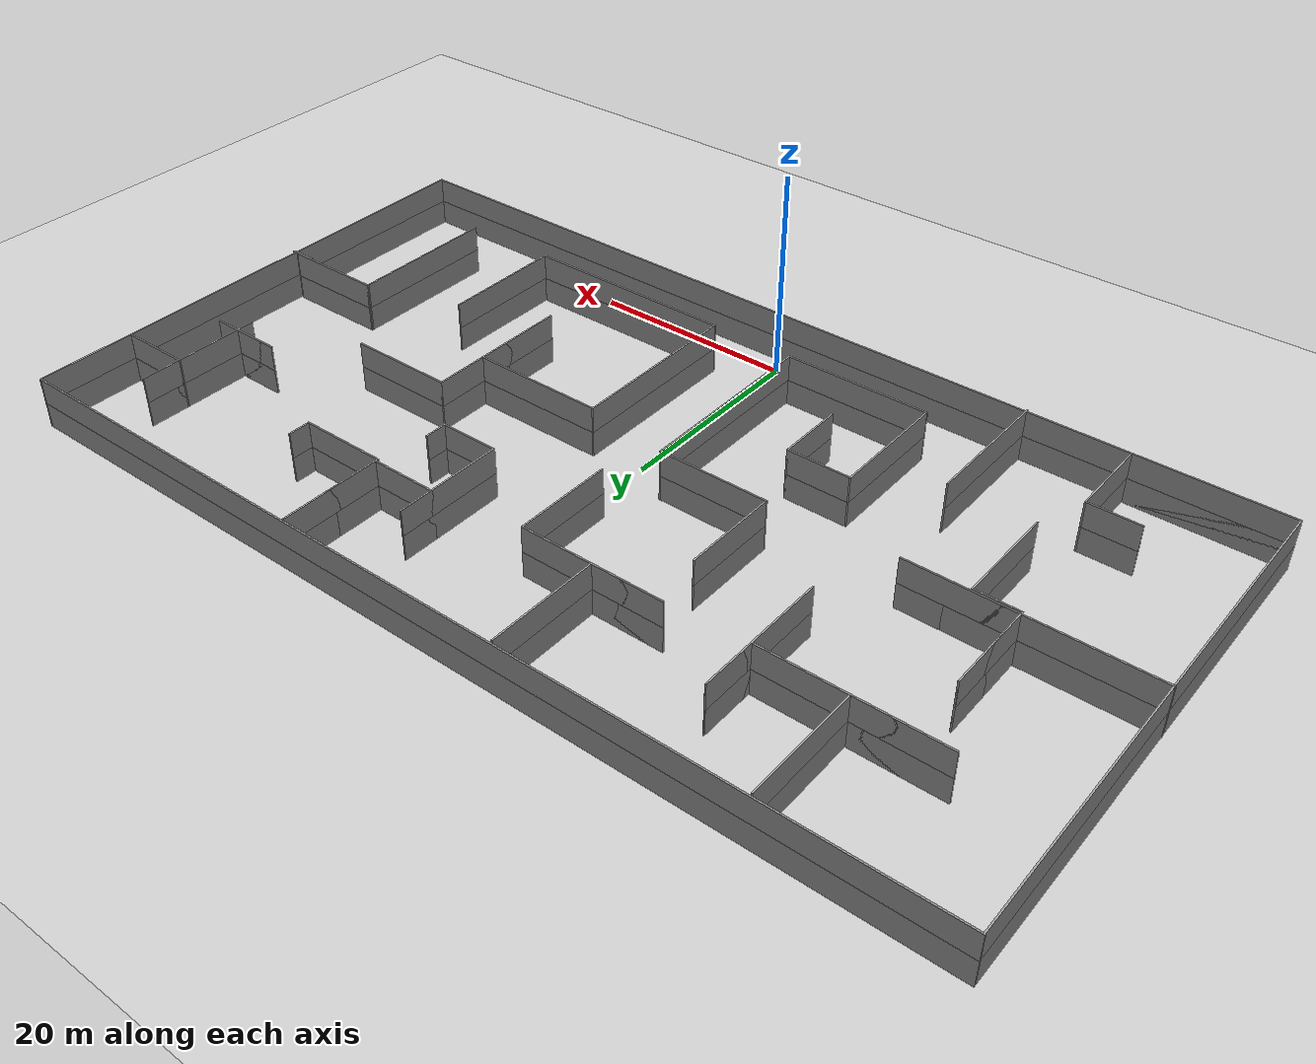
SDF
<sdf version="1.6">
 <world name="default">
  <light name="sun" type="directional">
   <pose>0 0 10 0 -0 0</pose>
   <diffuse>0.8 0.8 0.8 1</diffuse>
   <specular>0.2 0.2 0.2 1</specular>
   <attenuation>
    <range>1000</range>
    <constant>0.9</constant>
    <linear>0.01</linear>
    <quadratic>0.001</quadratic>
   </attenuation>
   <direction>-0.5 0.1 -0.9</direction>
  </light>
  <model name="ground_plane">
   <static>1</static>
   <link name="link">
    <collision name="collision">
     <geometry><plane><normal>0 0 1</normal><size>100 100</size></plane></geometry>
     <surface><friction><ode><mu>100</mu><mu2>50</mu2></ode></friction></surface>
    </collision>
    <visual name="visual">
     <cast_shadows>0</cast_shadows>
     <geometry><plane><normal>0 0 1</normal><size>100 100</size></plane></geometry>
     <material>
      <script><uri>file://media/materials/scripts/gazebo.material</uri><name>Gazebo/Grey</name></script>
     </material>
    </visual>
   </link>
  </model>
  <gravity>0 0 -9.8</gravity>
  <magnetic_field>6e-06 2.3e-05 -4.2e-05</magnetic_field>
  <atmosphere type="adiabatic"/>
  <physics name="default_physics" default="0" type="ode">
   <max_step_size>0.001</max_step_size>
   <real_time_factor>1</real_time_factor>
   <real_time_update_rate>1000</real_time_update_rate>
  </physics>
  <scene><ambient>0.4 0.4 0.4 1</ambient><background>0.7 0.7 0.7 1</background><shadows>1</shadows></scene>
  <audio><device>default</device></audio>
  <spherical_coordinates>
   <surface_model>EARTH_WGS84</surface_model>
   <latitude_deg>0</latitude_deg>
   <longitude_deg>0</longitude_deg>
   <elevation>0</elevation>
   <heading_deg>0</heading_deg>
  </spherical_coordinates>
  <model name="PaperTestRoom2">
   <pose>-1.27358 20.4941 0 0 -0 0</pose>
   <link name="Wall_10">
    <collision name="Wall_10_Collision">
     <geometry><box><size>14.25 0.15 2.5</size></box></geometry>
     <pose>0 0 1.25 0 -0 0</pose>
    </collision>
    <visual name="Wall_10_Visual">
     <pose>0 0 1.25 0 -0 0</pose>
     <geometry><box><size>14.25 0.15 2.5</size></box></geometry>
     <material>
      <script><uri>file://media/materials/scripts/gazebo.material</uri><name>Gazebo/Grey</name></script>
      <ambient>1 1 1 1</ambient>
     </material>
     <meta><layer>0</layer></meta>
    </visual>
    <pose>-39.665 -22.375 0 0 -0 0</pose>
   </link>
   <link name="Wall_11">
    <collision name="Wall_11_Collision">
     <geometry><box><size>8.5 0.15 2.5</size></box></geometry>
     <pose>0 0 1.25 0 -0 0</pose>
    </collision>
    <visual name="Wall_11_Visual">
     <pose>0 0 1.25 0 -0 0</pose>
     <geometry><box><size>8.5 0.15 2.5</size></box></geometry>
     <material>
      <script><uri>file://media/materials/scripts/gazebo.material</uri><name>Gazebo/Grey</name></script>
      <ambient>1 1 1 1</ambient>
     </material>
     <meta><layer>0</layer></meta>
    </visual>
    <pose>-32.615 -18.2 0 0 -0 1.5708</pose>
   </link>
   <link name="Wall_12">
    <collision name="Wall_12_Collision">
     <geometry><box><size>5 0.15 2.5</size></box></geometry>
     <pose>0 0 1.25 0 -0 0</pose>
    </collision>
    <visual name="Wall_12_Visual">
     <pose>0 0 1.25 0 -0 0</pose>
     <geometry><box><size>5 0.15 2.5</size></box></geometry>
     <material>
      <script><uri>file://media/materials/scripts/gazebo.material</uri><name>Gazebo/Grey</name></script>
      <ambient>1 1 1 1</ambient>
     </material>
     <meta><layer>0</layer></meta>
    </visual>
    <pose>-35.04 -14.025 0 0 -0 3.14159</pose>
   </link>
   <link name="Wall_14">
    <collision name="Wall_14_Collision">
     <geometry><box><size>13.5 0.15 2.5</size></box></geometry>
     <pose>0 0 1.25 0 -0 0</pose>
    </collision>
    <visual name="Wall_14_Visual">
     <pose>0 0 1.25 0 -0 0</pose>
     <geometry><box><size>13.5 0.15 2.5</size></box></geometry>
     <material>
      <script><uri>file://media/materials/scripts/gazebo.material</uri><name>Gazebo/Grey</name></script>
      <ambient>1 1 1 1</ambient>
     </material>
     <meta><layer>0</layer></meta>
    </visual>
    <pose>-22.9755 -15.9599 0 0 -0 1.5708</pose>
   </link>
   <link name="Wall_17">
    <collision name="Wall_17_Collision">
     <geometry><box><size>14.25 0.15 2.5</size></box></geometry>
     <pose>0 0 1.25 0 -0 0</pose>
    </collision>
    <visual name="Wall_17_Visual">
     <pose>0 0 1.25 0 -0 0</pose>
     <geometry><box><size>14.25 0.15 2.5</size></box></geometry>
     <material>
      <script><uri>file://media/materials/scripts/gazebo.material</uri><name>Gazebo/Grey</name></script>
      <ambient>1 1 1 1</ambient>
     </material>
     <meta><layer>0</layer></meta>
    </visual>
    <pose>-9.45369 -16.8689 0 0 -0 0</pose>
   </link>
   <link name="Wall_18">
    <collision name="Wall_18_Collision">
     <geometry><box><size>18.75 0.15 2.5</size></box></geometry>
     <pose>0 0 1.25 0 -0 0</pose>
    </collision>
    <visual name="Wall_18_Visual">
     <pose>0 0 1.25 0 -0 0</pose>
     <geometry><box><size>18.75 0.15 2.5</size></box></geometry>
     <material>
      <script><uri>file://media/materials/scripts/gazebo.material</uri><name>Gazebo/Grey</name></script>
      <ambient>1 1 1 1</ambient>
     </material>
     <meta><layer>0</layer></meta>
    </visual>
    <pose>-2.40369 -7.56892 0 0 -0 1.5708</pose>
   </link>
   <link name="Wall_19">
    <collision name="Wall_19_Collision">
     <geometry><box><size>10.75 0.15 2.5</size></box></geometry>
     <pose>0 0 1.25 0 -0 0</pose>
    </collision>
    <visual name="Wall_19_Visual">
     <pose>0 0 1.25 0 -0 0</pose>
     <geometry><box><size>10.75 0.15 2.5</size></box></geometry>
     <material>
      <script><uri>file://media/materials/scripts/gazebo.material</uri><name>Gazebo/Grey</name></script>
      <ambient>1 1 1 1</ambient>
     </material>
     <meta><layer>0</layer></meta>
    </visual>
    <pose>-7.70369 1.73108 0 0 -0 3.14159</pose>
   </link>
   <link name="Wall_20">
    <collision name="Wall_20_Collision">
     <geometry><box><size>9.5 0.15 2.5</size></box></geometry>
     <pose>0 0 1.25 0 -0 0</pose>
    </collision>
    <visual name="Wall_20_Visual">
     <pose>0 0 1.25 0 -0 0</pose>
     <geometry><box><size>9.5 0.15 2.5</size></box></geometry>
     <material>
      <script><uri>file://media/materials/scripts/gazebo.material</uri><name>Gazebo/Grey</name></script>
      <ambient>1 1 1 1</ambient>
     </material>
     <meta><layer>0</layer></meta>
    </visual>
    <pose>-13.0037 6.40608 0 0 -0 1.5708</pose>
   </link>
   <link name="Wall_23">
    <collision name="Wall_23_Collision">
     <geometry><box><size>12 0.15 2.5</size></box></geometry>
     <pose>0 0 1.25 0 -0 0</pose>
    </collision>
    <visual name="Wall_23_Visual">
     <pose>0 0 1.25 0 -0 0</pose>
     <geometry><box><size>12 0.15 2.5</size></box></geometry>
     <material>
      <script><uri>file://media/materials/scripts/gazebo.material</uri><name>Gazebo/Grey</name></script>
      <ambient>1 1 1 1</ambient>
     </material>
     <meta><layer>0</layer></meta>
    </visual>
    <pose>-16.5037 -10.9439 0 0 -0 1.5708</pose>
   </link>
   <link name="Wall_24">
    <collision name="Wall_24_Collision">
     <geometry><box><size>6.25 0.15 2.5</size></box></geometry>
     <pose>0 0 1.25 0 -0 0</pose>
    </collision>
    <visual name="Wall_24_Visual">
     <pose>0 0 1.25 0 -0 0</pose>
     <geometry><box><size>6.25 0.15 2.5</size></box></geometry>
     <material>
      <script><uri>file://media/materials/scripts/gazebo.material</uri><name>Gazebo/Grey</name></script>
      <ambient>1 1 1 1</ambient>
     </material>
     <meta><layer>0</layer></meta>
    </visual>
    <pose>-13.4537 -5.01892 0 0 -0 0</pose>
   </link>
   <link name="Wall_25">
    <collision name="Wall_25_Collision">
     <geometry><box><size>6.75 0.15 2.5</size></box></geometry>
     <pose>0 0 1.25 0 -0 0</pose>
    </collision>
    <visual name="Wall_25_Visual">
     <pose>0 0 1.25 0 -0 0</pose>
     <geometry><box><size>6.75 0.15 2.5</size></box></geometry>
     <material>
      <script><uri>file://media/materials/scripts/gazebo.material</uri><name>Gazebo/Grey</name></script>
      <ambient>1 1 1 1</ambient>
     </material>
     <meta><layer>0</layer></meta>
    </visual>
    <pose>-10.4037 -8.31892 0 0 -0 -1.5708</pose>
   </link>
   <link name="Wall_30">
    <collision name="Wall_30_Collision">
     <geometry><box><size>21 0.15 2.5</size></box></geometry>
     <pose>0 0 1.25 0 -0 0</pose>
    </collision>
    <visual name="Wall_30_Visual">
     <pose>0 0 1.25 0 -0 0</pose>
     <geometry><box><size>21 0.15 2.5</size></box></geometry>
     <material>
      <script><uri>file://media/materials/scripts/gazebo.material</uri><name>Gazebo/Grey</name></script>
      <ambient>1 1 1 1</ambient>
     </material>
     <meta><layer>0</layer></meta>
    </visual>
    <pose>16.3713 -16.8689 0 0 -0 0</pose>
   </link>
   <link name="Wall_31">
    <collision name="Wall_31_Collision">
     <geometry><box><size>12.25 0.15 2.5</size></box></geometry>
     <pose>0 0 1.25 0 -0 0</pose>
    </collision>
    <visual name="Wall_31_Visual">
     <pose>0 0 1.25 0 -0 0</pose>
     <geometry><box><size>12.25 0.15 2.5</size></box></geometry>
     <material>
      <script><uri>file://media/materials/scripts/gazebo.material</uri><name>Gazebo/Grey</name></script>
      <ambient>1 1 1 1</ambient>
     </material>
     <meta><layer>0</layer></meta>
    </visual>
    <pose>26.7963 -10.8189 0 0 -0 1.5708</pose>
   </link>
   <link name="Wall_34">
    <collision name="Wall_34_Collision">
     <geometry><box><size>17.5 0.15 2.5</size></box></geometry>
     <pose>0 0 1.25 0 -0 0</pose>
    </collision>
    <visual name="Wall_34_Visual">
     <pose>0 0 1.25 0 -0 0</pose>
     <geometry><box><size>17.5 0.15 2.5</size></box></geometry>
     <material>
      <script><uri>file://media/materials/scripts/gazebo.material</uri><name>Gazebo/Grey</name></script>
      <ambient>1 1 1 1</ambient>
     </material>
     <meta><layer>0</layer></meta>
    </visual>
    <pose>5.94631 -8.19392 0 0 -0 1.5708</pose>
   </link>
   <link name="Wall_35">
    <collision name="Wall_35_Collision">
     <geometry><box><size>13 0.15 2.5</size></box></geometry>
     <pose>0 0 1.25 0 -0 0</pose>
    </collision>
    <visual name="Wall_35_Visual">
     <pose>0 0 1.25 0 -0 0</pose>
     <geometry><box><size>13 0.15 2.5</size></box></geometry>
     <material>
      <script><uri>file://media/materials/scripts/gazebo.material</uri><name>Gazebo/Grey</name></script>
      <ambient>1 1 1 1</ambient>
     </material>
     <meta><layer>0</layer></meta>
    </visual>
    <pose>12.3713 0.481076 0 0 -0 0</pose>
   </link>
   <link name="Wall_36">
    <collision name="Wall_36_Collision">
     <geometry><box><size>9.25 0.15 2.5</size></box></geometry>
     <pose>0 0 1.25 0 -0 0</pose>
    </collision>
    <visual name="Wall_36_Visual">
     <pose>0 0 1.25 0 -0 0</pose>
     <geometry><box><size>9.25 0.15 2.5</size></box></geometry>
     <material>
      <script><uri>file://media/materials/scripts/gazebo.material</uri><name>Gazebo/Grey</name></script>
      <ambient>1 1 1 1</ambient>
     </material>
     <meta><layer>0</layer></meta>
    </visual>
    <pose>18.7963 -4.06892 0 0 -0 -1.5708</pose>
   </link>
   <link name="Wall_37">
    <collision name="Wall_37_Collision">
     <geometry><box><size>14.5 0.15 2.5</size></box></geometry>
     <pose>0 0 1.25 0 -0 0</pose>
    </collision>
    <visual name="Wall_37_Visual">
     <pose>0 0 1.25 0 -0 0</pose>
     <geometry><box><size>14.5 0.15 2.5</size></box></geometry>
     <material>
      <script><uri>file://media/materials/scripts/gazebo.material</uri><name>Gazebo/Grey</name></script>
      <ambient>1 1 1 1</ambient>
     </material>
     <meta><layer>0</layer></meta>
    </visual>
    <pose>18.7963 -1.44392 0 0 -0 1.5708</pose>
   </link>
   <link name="Wall_38">
    <collision name="Wall_38_Collision">
     <geometry><box><size>10.25 0.15 2.5</size></box></geometry>
     <pose>0 0 1.25 0 -0 0</pose>
    </collision>
    <visual name="Wall_38_Visual">
     <pose>0 0 1.25 0 -0 0</pose>
     <geometry><box><size>10.25 0.15 2.5</size></box></geometry>
     <material>
      <script><uri>file://media/materials/scripts/gazebo.material</uri><name>Gazebo/Grey</name></script>
      <ambient>1 1 1 1</ambient>
     </material>
     <meta><layer>0</layer></meta>
    </visual>
    <pose>23.8463 5.73108 0 0 -0 0</pose>
   </link>
   <link name="Wall_41">
    <collision name="Wall_41_Collision">
     <geometry><box><size>15 0.15 2.5</size></box></geometry>
     <pose>0 0 1.25 0 -0 0</pose>
    </collision>
    <visual name="Wall_41_Visual">
     <pose>0 0 1.25 0 -0 0</pose>
     <geometry><box><size>15 0.15 2.5</size></box></geometry>
     <material>
      <script><uri>file://media/materials/scripts/gazebo.material</uri><name>Gazebo/Grey</name></script>
      <ambient>1 1 1 1</ambient>
     </material>
     <meta><layer>0</layer></meta>
    </visual>
    <pose>36.1307 -9.29131 0 0 -0 1.5708</pose>
   </link>
   <link name="Wall_42">
    <collision name="Wall_42_Collision">
     <geometry><box><size>10 0.15 2.5</size></box></geometry>
     <pose>0 0 1.25 0 -0 0</pose>
    </collision>
    <visual name="Wall_42_Visual">
     <pose>0 0 1.25 0 -0 0</pose>
     <geometry><box><size>10 0.15 2.5</size></box></geometry>
     <material>
      <script><uri>file://media/materials/scripts/gazebo.material</uri><name>Gazebo/Grey</name></script>
      <ambient>1 1 1 1</ambient>
     </material>
     <meta><layer>0</layer></meta>
    </visual>
    <pose>41.0556 -1.86631 0 0 -0 0</pose>
   </link>
   <link name="Wall_44">
    <collision name="Wall_44_Collision">
     <geometry><box><size>2.75 0.15 2.5</size></box></geometry>
     <pose>0 0 1.25 0 -0 0</pose>
    </collision>
    <visual name="Wall_44_Visual">
     <pose>0 0 1.25 0 -0 0</pose>
     <geometry><box><size>2.75 0.15 2.5</size></box></geometry>
     <material>
      <script><uri>file://media/materials/scripts/gazebo.material</uri><name>Gazebo/Grey</name></script>
      <ambient>1 1 1 1</ambient>
     </material>
     <meta><layer>0</layer></meta>
    </visual>
    <pose>45.4491 -1.98643 0 0 -0 0</pose>
   </link>
   <link name="Wall_48">
    <collision name="Wall_48_Collision">
     <geometry><box><size>7 0.15 2.5</size></box></geometry>
     <pose>0 0 1.25 0 -0 0</pose>
    </collision>
    <visual name="Wall_48_Visual">
     <pose>0 0 1.25 0 -0 0</pose>
     <geometry><box><size>7 0.15 2.5</size></box></geometry>
     <material>
      <script><uri>file://media/materials/scripts/gazebo.material</uri><name>Gazebo/Grey</name></script>
      <ambient>1 1 1 1</ambient>
     </material>
     <meta><layer>0</layer></meta>
    </visual>
    <pose>42.8737 17.9027 0 0 -0 3.14159</pose>
   </link>
   <link name="Wall_49">
    <collision name="Wall_49_Collision">
     <geometry><box><size>4 0.15 2.5</size></box></geometry>
     <pose>0 0 1.25 0 -0 0</pose>
    </collision>
    <visual name="Wall_49_Visual">
     <pose>0 0 1.25 0 -0 0</pose>
     <geometry><box><size>4 0.15 2.5</size></box></geometry>
     <material>
      <script><uri>file://media/materials/scripts/gazebo.material</uri><name>Gazebo/Grey</name></script>
      <ambient>1 1 1 1</ambient>
     </material>
     <meta><layer>0</layer></meta>
    </visual>
    <pose>39.4487 19.8277 0 0 -0 1.5708</pose>
   </link>
   <link name="Wall_50">
    <collision name="Wall_50_Collision">
     <geometry><box><size>12.25 0.15 2.5</size></box></geometry>
     <pose>0 0 1.25 0 -0 0</pose>
    </collision>
    <visual name="Wall_50_Visual">
     <pose>0 0 1.25 0 -0 0</pose>
     <geometry><box><size>12.25 0.15 2.5</size></box></geometry>
     <material>
      <script><uri>file://media/materials/scripts/gazebo.material</uri><name>Gazebo/Grey</name></script>
      <ambient>1 1 1 1</ambient>
     </material>
     <meta><layer>0</layer></meta>
    </visual>
    <pose>39.4487 15.7027 0 0 -0 -1.5708</pose>
   </link>
   <link name="Wall_51">
    <collision name="Wall_51_Collision">
     <geometry><box><size>1.75 0.15 2.5</size></box></geometry>
     <pose>0 0 1.25 0 -0 0</pose>
    </collision>
    <visual name="Wall_51_Visual">
     <pose>0 0 1.25 0 -0 0</pose>
     <geometry><box><size>1.75 0.15 2.5</size></box></geometry>
     <material>
      <script><uri>file://media/materials/scripts/gazebo.material</uri><name>Gazebo/Grey</name></script>
      <ambient>1 1 1 1</ambient>
     </material>
     <meta><layer>0</layer></meta>
    </visual>
    <pose>39.4487 10.4527 0 0 -0 1.5708</pose>
   </link>
   <link name="Wall_52">
    <collision name="Wall_52_Collision">
     <geometry><box><size>4.75 0.15 2.5</size></box></geometry>
     <pose>0 0 1.25 0 -0 0</pose>
    </collision>
    <visual name="Wall_52_Visual">
     <pose>0 0 1.25 0 -0 0</pose>
     <geometry><box><size>4.75 0.15 2.5</size></box></geometry>
     <material>
      <script><uri>file://media/materials/scripts/gazebo.material</uri><name>Gazebo/Grey</name></script>
      <ambient>1 1 1 1</ambient>
     </material>
     <meta><layer>0</layer></meta>
    </visual>
    <pose>37.1487 11.2527 0 0 -0 3.14159</pose>
   </link>
   <link name="Wall_53">
    <collision name="Wall_53_Collision">
     <geometry><box><size>7.25 0.15 2.5</size></box></geometry>
     <pose>0 0 1.25 0 -0 0</pose>
    </collision>
    <visual name="Wall_53_Visual">
     <pose>0 0 1.25 0 -0 0</pose>
     <geometry><box><size>7.25 0.15 2.5</size></box></geometry>
     <material>
      <script><uri>file://media/materials/scripts/gazebo.material</uri><name>Gazebo/Grey</name></script>
      <ambient>1 1 1 1</ambient>
     </material>
     <meta><layer>0</layer></meta>
    </visual>
    <pose>38.3987 11.2527 0 0 -0 0</pose>
   </link>
   <link name="Wall_56">
    <collision name="Wall_56_Collision">
     <geometry><box><size>2.25 0.15 2.5</size></box></geometry>
     <pose>0 0 1.25 0 -0 0</pose>
    </collision>
    <visual name="Wall_56_Visual">
     <pose>0 0 1.25 0 -0 0</pose>
     <geometry><box><size>2.25 0.15 2.5</size></box></geometry>
     <material>
      <script><uri>file://media/materials/scripts/gazebo.material</uri><name>Gazebo/Grey</name></script>
      <ambient>1 1 1 1</ambient>
     </material>
     <meta><layer>0</layer></meta>
    </visual>
    <pose>23.1582 18.2121 0 0 -0 -1.5708</pose>
   </link>
   <link name="Wall_57">
    <collision name="Wall_57_Collision">
     <geometry><box><size>8.5 0.15 2.5</size></box></geometry>
     <pose>0 0 1.25 0 -0 0</pose>
    </collision>
    <visual name="Wall_57_Visual">
     <pose>0 0 1.25 0 -0 0</pose>
     <geometry><box><size>8.5 0.15 2.5</size></box></geometry>
     <material>
      <script><uri>file://media/materials/scripts/gazebo.material</uri><name>Gazebo/Grey</name></script>
      <ambient>1 1 1 1</ambient>
     </material>
     <meta><layer>0</layer></meta>
    </visual>
    <pose>18.9832 17.1621 0 0 -0 3.14159</pose>
   </link>
   <link name="Wall_58">
    <collision name="Wall_58_Collision">
     <geometry><box><size>10.25 0.15 2.5</size></box></geometry>
     <pose>0 0 1.25 0 -0 0</pose>
    </collision>
    <visual name="Wall_58_Visual">
     <pose>0 0 1.25 0 -0 0</pose>
     <geometry><box><size>10.25 0.15 2.5</size></box></geometry>
     <material>
      <script><uri>file://media/materials/scripts/gazebo.material</uri><name>Gazebo/Grey</name></script>
      <ambient>1 1 1 1</ambient>
     </material>
     <meta><layer>0</layer></meta>
    </visual>
    <pose>14.8082 22.2121 0 0 -0 1.5708</pose>
   </link>
   <link name="Wall_59">
    <collision name="Wall_59_Collision">
     <geometry><box><size>10 0.15 2.5</size></box></geometry>
     <pose>0 0 1.25 0 -0 0</pose>
    </collision>
    <visual name="Wall_59_Visual">
     <pose>0 0 1.25 0 -0 0</pose>
     <geometry><box><size>10 0.15 2.5</size></box></geometry>
     <material>
      <script><uri>file://media/materials/scripts/gazebo.material</uri><name>Gazebo/Grey</name></script>
      <ambient>1 1 1 1</ambient>
     </material>
     <meta><layer>0</layer></meta>
    </visual>
    <pose>14.8082 22.3371 0 0 -0 -1.5708</pose>
   </link>
   <link name="Wall_6">
    <collision name="Wall_6_Collision">
     <geometry><box><size>93 0.15 2.5</size></box></geometry>
     <pose>0 0 1.25 0 -0 0</pose>
    </collision>
    <visual name="Wall_6_Visual">
     <pose>0 0 1.25 0 -0 0</pose>
     <geometry><box><size>93 0.15 2.5</size></box></geometry>
     <material>
      <script><uri>file://media/materials/scripts/gazebo.material</uri><name>Gazebo/Grey</name></script>
      <ambient>1 1 1 1</ambient>
     </material>
     <meta><layer>0</layer></meta>
    </visual>
    <pose>-0.040017 -22.375 0 0 -0 0</pose>
   </link>
   <link name="Wall_60">
    <collision name="Wall_60_Collision">
     <geometry><box><size>6.5 0.15 2.5</size></box></geometry>
     <pose>0 0 1.25 0 -0 0</pose>
    </collision>
    <visual name="Wall_60_Visual">
     <pose>0 0 1.25 0 -0 0</pose>
     <geometry><box><size>6.5 0.15 2.5</size></box></geometry>
     <material>
      <script><uri>file://media/materials/scripts/gazebo.material</uri><name>Gazebo/Grey</name></script>
      <ambient>1 1 1 1</ambient>
     </material>
     <meta><layer>0</layer></meta>
    </visual>
    <pose>11.6332 17.4121 0 0 -0 3.14159</pose>
   </link>
   <link name="Wall_61">
    <collision name="Wall_61_Collision">
     <geometry><box><size>3.5 0.15 2.5</size></box></geometry>
     <pose>0 0 1.25 0 -0 0</pose>
    </collision>
    <visual name="Wall_61_Visual">
     <pose>0 0 1.25 0 -0 0</pose>
     <geometry><box><size>3.5 0.15 2.5</size></box></geometry>
     <material>
      <script><uri>file://media/materials/scripts/gazebo.material</uri><name>Gazebo/Grey</name></script>
      <ambient>1 1 1 1</ambient>
     </material>
     <meta><layer>0</layer></meta>
    </visual>
    <pose>8.45816 19.0871 0 0 -0 1.5708</pose>
   </link>
   <link name="Wall_62">
    <collision name="Wall_62_Collision">
     <geometry><box><size>10.75 0.15 2.5</size></box></geometry>
     <pose>0 0 1.25 0 -0 0</pose>
    </collision>
    <visual name="Wall_62_Visual">
     <pose>0 0 1.25 0 -0 0</pose>
     <geometry><box><size>10.75 0.15 2.5</size></box></geometry>
     <material>
      <script><uri>file://media/materials/scripts/gazebo.material</uri><name>Gazebo/Grey</name></script>
      <ambient>1 1 1 1</ambient>
     </material>
     <meta><layer>0</layer></meta>
    </visual>
    <pose>8.45816 15.4621 0 0 -0 -1.5708</pose>
   </link>
   <link name="Wall_63">
    <collision name="Wall_63_Collision">
     <geometry><box><size>5.75 0.15 2.5</size></box></geometry>
     <pose>0 0 1.25 0 -0 0</pose>
    </collision>
    <visual name="Wall_63_Visual">
     <pose>0 0 1.25 0 -0 0</pose>
     <geometry><box><size>5.75 0.15 2.5</size></box></geometry>
     <material>
      <script><uri>file://media/materials/scripts/gazebo.material</uri><name>Gazebo/Grey</name></script>
      <ambient>1 1 1 1</ambient>
     </material>
     <meta><layer>0</layer></meta>
    </visual>
    <pose>11.2582 10.1621 0 0 -0 0</pose>
   </link>
   <link name="Wall_64">
    <collision name="Wall_64_Collision">
     <geometry><box><size>2.25 0.15 2.5</size></box></geometry>
     <pose>0 0 1.25 0 -0 0</pose>
    </collision>
    <visual name="Wall_64_Visual">
     <pose>0 0 1.25 0 -0 0</pose>
     <geometry><box><size>2.25 0.15 2.5</size></box></geometry>
     <material>
      <script><uri>file://media/materials/scripts/gazebo.material</uri><name>Gazebo/Grey</name></script>
      <ambient>1 1 1 1</ambient>
     </material>
     <meta><layer>0</layer></meta>
    </visual>
    <pose>14.0582 11.2121 0 0 -0 1.5708</pose>
   </link>
   <link name="Wall_67">
    <collision name="Wall_67_Collision">
     <geometry><box><size>11 0.15 2.5</size></box></geometry>
     <pose>0 0 1.25 0 -0 0</pose>
    </collision>
    <visual name="Wall_67_Visual">
     <pose>0 0 1.25 0 -0 0</pose>
     <geometry><box><size>11 0.15 2.5</size></box></geometry>
     <material>
      <script><uri>file://media/materials/scripts/gazebo.material</uri><name>Gazebo/Grey</name></script>
      <ambient>1 1 1 1</ambient>
     </material>
     <meta><layer>0</layer></meta>
    </visual>
    <pose>-7.26444 21.7016 0 0 -0 -1.5708</pose>
   </link>
   <link name="Wall_68">
    <collision name="Wall_68_Collision">
     <geometry><box><size>7 0.15 2.5</size></box></geometry>
     <pose>0 0 1.25 0 -0 0</pose>
    </collision>
    <visual name="Wall_68_Visual">
     <pose>0 0 1.25 0 -0 0</pose>
     <geometry><box><size>7 0.15 2.5</size></box></geometry>
     <material>
      <script><uri>file://media/materials/scripts/gazebo.material</uri><name>Gazebo/Grey</name></script>
      <ambient>1 1 1 1</ambient>
     </material>
     <meta><layer>0</layer></meta>
    </visual>
    <pose>-10.6894 16.2766 0 0 -0 3.14159</pose>
   </link>
   <link name="Wall_69">
    <collision name="Wall_69_Collision">
     <geometry><box><size>14 0.15 2.5</size></box></geometry>
     <pose>0 0 1.25 0 -0 0</pose>
    </collision>
    <visual name="Wall_69_Visual">
     <pose>0 0 1.25 0 -0 0</pose>
     <geometry><box><size>14 0.15 2.5</size></box></geometry>
     <material>
      <script><uri>file://media/materials/scripts/gazebo.material</uri><name>Gazebo/Grey</name></script>
      <ambient>1 1 1 1</ambient>
     </material>
     <meta><layer>0</layer></meta>
    </visual>
    <pose>-7.18944 16.2766 0 0 -0 0</pose>
   </link>
   <link name="Wall_7">
    <collision name="Wall_7_Collision">
     <geometry><box><size>50 0.15 2.5</size></box></geometry>
     <pose>0 0 1.25 0 -0 0</pose>
    </collision>
    <visual name="Wall_7_Visual">
     <pose>0 0 1.25 0 -0 0</pose>
     <geometry><box><size>50 0.15 2.5</size></box></geometry>
     <material>
      <script><uri>file://media/materials/scripts/gazebo.material</uri><name>Gazebo/Grey</name></script>
      <ambient>1 1 1 1</ambient>
     </material>
     <meta><layer>0</layer></meta>
    </visual>
    <pose>46.385 2.55 0 0 -0 1.5708</pose>
   </link>
   <link name="Wall_70">
    <collision name="Wall_70_Collision">
     <geometry><box><size>9.75 0.15 2.5</size></box></geometry>
     <pose>0 0 1.25 0 -0 0</pose>
    </collision>
    <visual name="Wall_70_Visual">
     <pose>0 0 1.25 0 -0 0</pose>
     <geometry><box><size>9.75 0.15 2.5</size></box></geometry>
     <material>
      <script><uri>file://media/materials/scripts/gazebo.material</uri><name>Gazebo/Grey</name></script>
      <ambient>1 1 1 1</ambient>
     </material>
     <meta><layer>0</layer></meta>
    </visual>
    <pose>-0.264437 11.4766 0 0 -0 -1.5708</pose>
   </link>
   <link name="Wall_75">
    <collision name="Wall_75_Collision">
     <geometry><box><size>11.5 0.15 2.5</size></box></geometry>
     <pose>0 0 1.25 0 -0 0</pose>
    </collision>
    <visual name="Wall_75_Visual">
     <pose>0 0 1.25 0 -0 0</pose>
     <geometry><box><size>11.5 0.15 2.5</size></box></geometry>
     <material>
      <script><uri>file://media/materials/scripts/gazebo.material</uri><name>Gazebo/Grey</name></script>
      <ambient>1 1 1 1</ambient>
     </material>
     <meta><layer>0</layer></meta>
    </visual>
    <pose>-29.9196 21.4516 0 0 -0 -1.5708</pose>
   </link>
   <link name="Wall_76">
    <collision name="Wall_76_Collision">
     <geometry><box><size>8.5 0.15 2.5</size></box></geometry>
     <pose>0 0 1.25 0 -0 0</pose>
    </collision>
    <visual name="Wall_76_Visual">
     <pose>0 0 1.25 0 -0 0</pose>
     <geometry><box><size>8.5 0.15 2.5</size></box></geometry>
     <material>
      <script><uri>file://media/materials/scripts/gazebo.material</uri><name>Gazebo/Grey</name></script>
      <ambient>1 1 1 1</ambient>
     </material>
     <meta><layer>0</layer></meta>
    </visual>
    <pose>-34.0946 15.7766 0 0 -0 3.14159</pose>
   </link>
   <link name="Wall_77">
    <collision name="Wall_77_Collision">
     <geometry><box><size>16.75 0.15 2.5</size></box></geometry>
     <pose>0 0 1.25 0 -0 0</pose>
    </collision>
    <visual name="Wall_77_Visual">
     <pose>0 0 1.25 0 -0 0</pose>
     <geometry><box><size>16.75 0.15 2.5</size></box></geometry>
     <material>
      <script><uri>file://media/materials/scripts/gazebo.material</uri><name>Gazebo/Grey</name></script>
      <ambient>1 1 1 1</ambient>
     </material>
     <meta><layer>0</layer></meta>
    </visual>
    <pose>-29.9696 15.7766 0 0 -0 0</pose>
   </link>
   <link name="Wall_78">
    <collision name="Wall_78_Collision">
     <geometry><box><size>5.5 0.15 2.5</size></box></geometry>
     <pose>0 0 1.25 0 -0 0</pose>
    </collision>
    <visual name="Wall_78_Visual">
     <pose>0 0 1.25 0 -0 0</pose>
     <geometry><box><size>5.5 0.15 2.5</size></box></geometry>
     <material>
      <script><uri>file://media/materials/scripts/gazebo.material</uri><name>Gazebo/Grey</name></script>
      <ambient>1 1 1 1</ambient>
     </material>
     <meta><layer>0</layer></meta>
    </visual>
    <pose>-21.6696 18.4516 0 0 -0 1.5708</pose>
   </link>
   <link name="Wall_79">
    <collision name="Wall_79_Collision">
     <geometry><box><size>13.25 0.15 2.5</size></box></geometry>
     <pose>0 0 1.25 0 -0 0</pose>
    </collision>
    <visual name="Wall_79_Visual">
     <pose>0 0 1.25 0 -0 0</pose>
     <geometry><box><size>13.25 0.15 2.5</size></box></geometry>
     <material>
      <script><uri>file://media/materials/scripts/gazebo.material</uri><name>Gazebo/Grey</name></script>
      <ambient>1 1 1 1</ambient>
     </material>
     <meta><layer>0</layer></meta>
    </visual>
    <pose>-21.6696 14.5766 0 0 -0 -1.5708</pose>
   </link>
   <link name="Wall_8">
    <collision name="Wall_8_Collision">
     <geometry><box><size>93.25 0.15 2.5</size></box></geometry>
     <pose>0 0 1.25 0 -0 0</pose>
    </collision>
    <visual name="Wall_8_Visual">
     <pose>0 0 1.25 0 -0 0</pose>
     <geometry><box><size>93.25 0.15 2.5</size></box></geometry>
     <material>
      <script><uri>file://media/materials/scripts/gazebo.material</uri><name>Gazebo/Grey</name></script>
      <ambient>1 1 1 1</ambient>
     </material>
     <meta><layer>0</layer></meta>
    </visual>
    <pose>-0.165017 27.475 0 0 -0 3.14159</pose>
   </link>
   <link name="Wall_84">
    <collision name="Wall_84_Collision">
     <geometry><box><size>22 0.15 2.5</size></box></geometry>
     <pose>0 0 1.25 0 -0 0</pose>
    </collision>
    <visual name="Wall_84_Visual">
     <pose>0 0 1.25 0 -0 0</pose>
     <geometry><box><size>22 0.15 2.5</size></box></geometry>
     <material>
      <script><uri>file://media/materials/scripts/gazebo.material</uri><name>Gazebo/Grey</name></script>
      <ambient>1 1 1 1</ambient>
     </material>
     <meta><layer>0</layer></meta>
    </visual>
    <pose>-35.8241 1.07321 0 0 -0 0</pose>
   </link>
   <link name="Wall_85">
    <collision name="Wall_85_Collision">
     <geometry><box><size>10.25 0.15 2.5</size></box></geometry>
     <pose>0 0 1.25 0 -0 0</pose>
    </collision>
    <visual name="Wall_85_Visual">
     <pose>0 0 1.25 0 -0 0</pose>
     <geometry><box><size>10.25 0.15 2.5</size></box></geometry>
     <material>
      <script><uri>file://media/materials/scripts/gazebo.material</uri><name>Gazebo/Grey</name></script>
      <ambient>1 1 1 1</ambient>
     </material>
     <meta><layer>0</layer></meta>
    </visual>
    <pose>-29.9491 1.07321 0 0 -0 3.14159</pose>
   </link>
   <link name="Wall_86">
    <collision name="Wall_86_Collision">
     <geometry><box><size>9 0.15 2.5</size></box></geometry>
     <pose>0 0 1.25 0 -0 0</pose>
    </collision>
    <visual name="Wall_86_Visual">
     <pose>0 0 1.25 0 -0 0</pose>
     <geometry><box><size>9 0.15 2.5</size></box></geometry>
     <material>
      <script><uri>file://media/materials/scripts/gazebo.material</uri><name>Gazebo/Grey</name></script>
      <ambient>1 1 1 1</ambient>
     </material>
     <meta><layer>0</layer></meta>
    </visual>
    <pose>-34.9991 5.49821 0 0 -0 1.5708</pose>
   </link>
   <link name="Wall_87">
    <collision name="Wall_87_Collision">
     <geometry><box><size>9.25 0.15 2.5</size></box></geometry>
     <pose>0 0 1.25 0 -0 0</pose>
    </collision>
    <visual name="Wall_87_Visual">
     <pose>0 0 1.25 0 -0 0</pose>
     <geometry><box><size>9.25 0.15 2.5</size></box></geometry>
     <material>
      <script><uri>file://media/materials/scripts/gazebo.material</uri><name>Gazebo/Grey</name></script>
      <ambient>1 1 1 1</ambient>
     </material>
     <meta><layer>0</layer></meta>
    </visual>
    <pose>-34.9991 5.37321 0 0 -0 -1.5708</pose>
   </link>
   <link name="Wall_88">
    <collision name="Wall_88_Collision">
     <geometry><box><size>4.25 0.15 2.5</size></box></geometry>
     <pose>0 0 1.25 0 -0 0</pose>
    </collision>
    <visual name="Wall_88_Visual">
     <pose>0 0 1.25 0 -0 0</pose>
     <geometry><box><size>4.25 0.15 2.5</size></box></geometry>
     <material>
      <script><uri>file://media/materials/scripts/gazebo.material</uri><name>Gazebo/Grey</name></script>
      <ambient>1 1 1 1</ambient>
     </material>
     <meta><layer>0</layer></meta>
    </visual>
    <pose>-32.9491 0.82321 0 0 -0 0</pose>
   </link>
   <link name="Wall_89">
    <collision name="Wall_89_Collision">
     <geometry><box><size>10.25 0.15 2.5</size></box></geometry>
     <pose>0 0 1.25 0 -0 0</pose>
    </collision>
    <visual name="Wall_89_Visual">
     <pose>0 0 1.25 0 -0 0</pose>
     <geometry><box><size>10.25 0.15 2.5</size></box></geometry>
     <material>
      <script><uri>file://media/materials/scripts/gazebo.material</uri><name>Gazebo/Grey</name></script>
      <ambient>1 1 1 1</ambient>
     </material>
     <meta><layer>0</layer></meta>
    </visual>
    <pose>-30.8991 -4.22679 0 0 -0 -1.5708</pose>
   </link>
   <link name="Wall_9">
    <collision name="Wall_9_Collision">
     <geometry><box><size>50 0.15 2.5</size></box></geometry>
     <pose>0 0 1.25 0 -0 0</pose>
    </collision>
    <visual name="Wall_9_Visual">
     <pose>0 0 1.25 0 -0 0</pose>
     <geometry><box><size>50 0.15 2.5</size></box></geometry>
     <material>
      <script><uri>file://media/materials/scripts/gazebo.material</uri><name>Gazebo/Grey</name></script>
      <ambient>1 1 1 1</ambient>
     </material>
     <meta><layer>0</layer></meta>
    </visual>
    <pose>-46.715 2.55 0 0 -0 -1.5708</pose>
   </link>
   <static>1</static>
  </model>
  <model name="PaperTestRoom2_clone">
   <pose>-1.27358 20.494 2.5 0 -0 0</pose>
   <link name="Wall_10">
    <collision name="Wall_10_Collision">
     <geometry><box><size>14.25 0.15 2.5</size></box></geometry>
     <pose>0 0 1.25 0 -0 0</pose>
    </collision>
    <visual name="Wall_10_Visual">
     <pose>0 0 1.25 0 -0 0</pose>
     <geometry><box><size>14.25 0.15 2.5</size></box></geometry>
     <material>
      <script><uri>file://media/materials/scripts/gazebo.material</uri><name>Gazebo/Grey</name></script>
      <ambient>1 1 1 1</ambient>
     </material>
     <meta><layer>0</layer></meta>
    </visual>
    <pose>-39.665 -22.375 0 0 -0 0</pose>
   </link>
   <link name="Wall_11">
    <collision name="Wall_11_Collision">
     <geometry><box><size>8.5 0.15 2.5</size></box></geometry>
     <pose>0 0 1.25 0 -0 0</pose>
    </collision>
    <visual name="Wall_11_Visual">
     <pose>0 0 1.25 0 -0 0</pose>
     <geometry><box><size>8.5 0.15 2.5</size></box></geometry>
     <material>
      <script><uri>file://media/materials/scripts/gazebo.material</uri><name>Gazebo/Grey</name></script>
      <ambient>1 1 1 1</ambient>
     </material>
     <meta><layer>0</layer></meta>
    </visual>
    <pose>-32.615 -18.2 0 0 -0 1.5708</pose>
   </link>
   <link name="Wall_12">
    <collision name="Wall_12_Collision">
     <geometry><box><size>5 0.15 2.5</size></box></geometry>
     <pose>0 0 1.25 0 -0 0</pose>
    </collision>
    <visual name="Wall_12_Visual">
     <pose>0 0 1.25 0 -0 0</pose>
     <geometry><box><size>5 0.15 2.5</size></box></geometry>
     <material>
      <script><uri>file://media/materials/scripts/gazebo.material</uri><name>Gazebo/Grey</name></script>
      <ambient>1 1 1 1</ambient>
     </material>
     <meta><layer>0</layer></meta>
    </visual>
    <pose>-35.04 -14.025 0 0 -0 3.14159</pose>
   </link>
   <link name="Wall_14">
    <collision name="Wall_14_Collision">
     <geometry><box><size>13.5 0.15 2.5</size></box></geometry>
     <pose>0 0 1.25 0 -0 0</pose>
    </collision>
    <visual name="Wall_14_Visual">
     <pose>0 0 1.25 0 -0 0</pose>
     <geometry><box><size>13.5 0.15 2.5</size></box></geometry>
     <material>
      <script><uri>file://media/materials/scripts/gazebo.material</uri><name>Gazebo/Grey</name></script>
      <ambient>1 1 1 1</ambient>
     </material>
     <meta><layer>0</layer></meta>
    </visual>
    <pose>-22.9755 -15.9599 0 0 -0 1.5708</pose>
   </link>
   <link name="Wall_17">
    <collision name="Wall_17_Collision">
     <geometry><box><size>14.25 0.15 2.5</size></box></geometry>
     <pose>0 0 1.25 0 -0 0</pose>
    </collision>
    <visual name="Wall_17_Visual">
     <pose>0 0 1.25 0 -0 0</pose>
     <geometry><box><size>14.25 0.15 2.5</size></box></geometry>
     <material>
      <script><uri>file://media/materials/scripts/gazebo.material</uri><name>Gazebo/Grey</name></script>
      <ambient>1 1 1 1</ambient>
     </material>
     <meta><layer>0</layer></meta>
    </visual>
    <pose>-9.45369 -16.8689 0 0 -0 0</pose>
   </link>
   <link name="Wall_18">
    <collision name="Wall_18_Collision">
     <geometry><box><size>18.75 0.15 2.5</size></box></geometry>
     <pose>0 0 1.25 0 -0 0</pose>
    </collision>
    <visual name="Wall_18_Visual">
     <pose>0 0 1.25 0 -0 0</pose>
     <geometry><box><size>18.75 0.15 2.5</size></box></geometry>
     <material>
      <script><uri>file://media/materials/scripts/gazebo.material</uri><name>Gazebo/Grey</name></script>
      <ambient>1 1 1 1</ambient>
     </material>
     <meta><layer>0</layer></meta>
    </visual>
    <pose>-2.40369 -7.56892 0 0 -0 1.5708</pose>
   </link>
   <link name="Wall_19">
    <collision name="Wall_19_Collision">
     <geometry><box><size>10.75 0.15 2.5</size></box></geometry>
     <pose>0 0 1.25 0 -0 0</pose>
    </collision>
    <visual name="Wall_19_Visual">
     <pose>0 0 1.25 0 -0 0</pose>
     <geometry><box><size>10.75 0.15 2.5</size></box></geometry>
     <material>
      <script><uri>file://media/materials/scripts/gazebo.material</uri><name>Gazebo/Grey</name></script>
      <ambient>1 1 1 1</ambient>
     </material>
     <meta><layer>0</layer></meta>
    </visual>
    <pose>-7.70369 1.73108 0 0 -0 3.14159</pose>
   </link>
   <link name="Wall_20">
    <collision name="Wall_20_Collision">
     <geometry><box><size>9.5 0.15 2.5</size></box></geometry>
     <pose>0 0 1.25 0 -0 0</pose>
    </collision>
    <visual name="Wall_20_Visual">
     <pose>0 0 1.25 0 -0 0</pose>
     <geometry><box><size>9.5 0.15 2.5</size></box></geometry>
     <material>
      <script><uri>file://media/materials/scripts/gazebo.material</uri><name>Gazebo/Grey</name></script>
      <ambient>1 1 1 1</ambient>
     </material>
     <meta><layer>0</layer></meta>
    </visual>
    <pose>-13.0037 6.40608 0 0 -0 1.5708</pose>
   </link>
   <link name="Wall_23">
    <collision name="Wall_23_Collision">
     <geometry><box><size>12 0.15 2.5</size></box></geometry>
     <pose>0 0 1.25 0 -0 0</pose>
    </collision>
    <visual name="Wall_23_Visual">
     <pose>0 0 1.25 0 -0 0</pose>
     <geometry><box><size>12 0.15 2.5</size></box></geometry>
     <material>
      <script><uri>file://media/materials/scripts/gazebo.material</uri><name>Gazebo/Grey</name></script>
      <ambient>1 1 1 1</ambient>
     </material>
     <meta><layer>0</layer></meta>
    </visual>
    <pose>-16.5037 -10.9439 0 0 -0 1.5708</pose>
   </link>
   <link name="Wall_24">
    <collision name="Wall_24_Collision">
     <geometry><box><size>6.25 0.15 2.5</size></box></geometry>
     <pose>0 0 1.25 0 -0 0</pose>
    </collision>
    <visual name="Wall_24_Visual">
     <pose>0 0 1.25 0 -0 0</pose>
     <geometry><box><size>6.25 0.15 2.5</size></box></geometry>
     <material>
      <script><uri>file://media/materials/scripts/gazebo.material</uri><name>Gazebo/Grey</name></script>
      <ambient>1 1 1 1</ambient>
     </material>
     <meta><layer>0</layer></meta>
    </visual>
    <pose>-13.4537 -5.01892 0 0 -0 0</pose>
   </link>
   <link name="Wall_25">
    <collision name="Wall_25_Collision">
     <geometry><box><size>6.75 0.15 2.5</size></box></geometry>
     <pose>0 0 1.25 0 -0 0</pose>
    </collision>
    <visual name="Wall_25_Visual">
     <pose>0 0 1.25 0 -0 0</pose>
     <geometry><box><size>6.75 0.15 2.5</size></box></geometry>
     <material>
      <script><uri>file://media/materials/scripts/gazebo.material</uri><name>Gazebo/Grey</name></script>
      <ambient>1 1 1 1</ambient>
     </material>
     <meta><layer>0</layer></meta>
    </visual>
    <pose>-10.4037 -8.31892 0 0 -0 -1.5708</pose>
   </link>
   <link name="Wall_30">
    <collision name="Wall_30_Collision">
     <geometry><box><size>21 0.15 2.5</size></box></geometry>
     <pose>0 0 1.25 0 -0 0</pose>
    </collision>
    <visual name="Wall_30_Visual">
     <pose>0 0 1.25 0 -0 0</pose>
     <geometry><box><size>21 0.15 2.5</size></box></geometry>
     <material>
      <script><uri>file://media/materials/scripts/gazebo.material</uri><name>Gazebo/Grey</name></script>
      <ambient>1 1 1 1</ambient>
     </material>
     <meta><layer>0</layer></meta>
    </visual>
    <pose>16.3713 -16.8689 0 0 -0 0</pose>
   </link>
   <link name="Wall_31">
    <collision name="Wall_31_Collision">
     <geometry><box><size>12.25 0.15 2.5</size></box></geometry>
     <pose>0 0 1.25 0 -0 0</pose>
    </collision>
    <visual name="Wall_31_Visual">
     <pose>0 0 1.25 0 -0 0</pose>
     <geometry><box><size>12.25 0.15 2.5</size></box></geometry>
     <material>
      <script><uri>file://media/materials/scripts/gazebo.material</uri><name>Gazebo/Grey</name></script>
      <ambient>1 1 1 1</ambient>
     </material>
     <meta><layer>0</layer></meta>
    </visual>
    <pose>26.7963 -10.8189 0 0 -0 1.5708</pose>
   </link>
   <link name="Wall_34">
    <collision name="Wall_34_Collision">
     <geometry><box><size>17.5 0.15 2.5</size></box></geometry>
     <pose>0 0 1.25 0 -0 0</pose>
    </collision>
    <visual name="Wall_34_Visual">
     <pose>0 0 1.25 0 -0 0</pose>
     <geometry><box><size>17.5 0.15 2.5</size></box></geometry>
     <material>
      <script><uri>file://media/materials/scripts/gazebo.material</uri><name>Gazebo/Grey</name></script>
      <ambient>1 1 1 1</ambient>
     </material>
     <meta><layer>0</layer></meta>
    </visual>
    <pose>5.94631 -8.19392 0 0 -0 1.5708</pose>
   </link>
   <link name="Wall_35">
    <collision name="Wall_35_Collision">
     <geometry><box><size>13 0.15 2.5</size></box></geometry>
     <pose>0 0 1.25 0 -0 0</pose>
    </collision>
    <visual name="Wall_35_Visual">
     <pose>0 0 1.25 0 -0 0</pose>
     <geometry><box><size>13 0.15 2.5</size></box></geometry>
     <material>
      <script><uri>file://media/materials/scripts/gazebo.material</uri><name>Gazebo/Grey</name></script>
      <ambient>1 1 1 1</ambient>
     </material>
     <meta><layer>0</layer></meta>
    </visual>
    <pose>12.3713 0.481076 0 0 -0 0</pose>
   </link>
   <link name="Wall_36">
    <collision name="Wall_36_Collision">
     <geometry><box><size>9.25 0.15 2.5</size></box></geometry>
     <pose>0 0 1.25 0 -0 0</pose>
    </collision>
    <visual name="Wall_36_Visual">
     <pose>0 0 1.25 0 -0 0</pose>
     <geometry><box><size>9.25 0.15 2.5</size></box></geometry>
     <material>
      <script><uri>file://media/materials/scripts/gazebo.material</uri><name>Gazebo/Grey</name></script>
      <ambient>1 1 1 1</ambient>
     </material>
     <meta><layer>0</layer></meta>
    </visual>
    <pose>18.7963 -4.06892 0 0 -0 -1.5708</pose>
   </link>
   <link name="Wall_37">
    <collision name="Wall_37_Collision">
     <geometry><box><size>14.5 0.15 2.5</size></box></geometry>
     <pose>0 0 1.25 0 -0 0</pose>
    </collision>
    <visual name="Wall_37_Visual">
     <pose>0 0 1.25 0 -0 0</pose>
     <geometry><box><size>14.5 0.15 2.5</size></box></geometry>
     <material>
      <script><uri>file://media/materials/scripts/gazebo.material</uri><name>Gazebo/Grey</name></script>
      <ambient>1 1 1 1</ambient>
     </material>
     <meta><layer>0</layer></meta>
    </visual>
    <pose>18.7963 -1.44392 0 0 -0 1.5708</pose>
   </link>
   <link name="Wall_38">
    <collision name="Wall_38_Collision">
     <geometry><box><size>10.25 0.15 2.5</size></box></geometry>
     <pose>0 0 1.25 0 -0 0</pose>
    </collision>
    <visual name="Wall_38_Visual">
     <pose>0 0 1.25 0 -0 0</pose>
     <geometry><box><size>10.25 0.15 2.5</size></box></geometry>
     <material>
      <script><uri>file://media/materials/scripts/gazebo.material</uri><name>Gazebo/Grey</name></script>
      <ambient>1 1 1 1</ambient>
     </material>
     <meta><layer>0</layer></meta>
    </visual>
    <pose>23.8463 5.73108 0 0 -0 0</pose>
   </link>
   <link name="Wall_41">
    <collision name="Wall_41_Collision">
     <geometry><box><size>15 0.15 2.5</size></box></geometry>
     <pose>0 0 1.25 0 -0 0</pose>
    </collision>
    <visual name="Wall_41_Visual">
     <pose>0 0 1.25 0 -0 0</pose>
     <geometry><box><size>15 0.15 2.5</size></box></geometry>
     <material>
      <script><uri>file://media/materials/scripts/gazebo.material</uri><name>Gazebo/Grey</name></script>
      <ambient>1 1 1 1</ambient>
     </material>
     <meta><layer>0</layer></meta>
    </visual>
    <pose>36.1307 -9.29131 0 0 -0 1.5708</pose>
   </link>
   <link name="Wall_42">
    <collision name="Wall_42_Collision">
     <geometry><box><size>10 0.15 2.5</size></box></geometry>
     <pose>0 0 1.25 0 -0 0</pose>
    </collision>
    <visual name="Wall_42_Visual">
     <pose>0 0 1.25 0 -0 0</pose>
     <geometry><box><size>10 0.15 2.5</size></box></geometry>
     <material>
      <script><uri>file://media/materials/scripts/gazebo.material</uri><name>Gazebo/Grey</name></script>
      <ambient>1 1 1 1</ambient>
     </material>
     <meta><layer>0</layer></meta>
    </visual>
    <pose>41.0556 -1.86631 0 0 -0 0</pose>
   </link>
   <link name="Wall_44">
    <collision name="Wall_44_Collision">
     <geometry><box><size>2.75 0.15 2.5</size></box></geometry>
     <pose>0 0 1.25 0 -0 0</pose>
    </collision>
    <visual name="Wall_44_Visual">
     <pose>0 0 1.25 0 -0 0</pose>
     <geometry><box><size>2.75 0.15 2.5</size></box></geometry>
     <material>
      <script><uri>file://media/materials/scripts/gazebo.material</uri><name>Gazebo/Grey</name></script>
      <ambient>1 1 1 1</ambient>
     </material>
     <meta><layer>0</layer></meta>
    </visual>
    <pose>45.4491 -1.98643 0 0 -0 0</pose>
   </link>
   <link name="Wall_48">
    <collision name="Wall_48_Collision">
     <geometry><box><size>7 0.15 2.5</size></box></geometry>
     <pose>0 0 1.25 0 -0 0</pose>
    </collision>
    <visual name="Wall_48_Visual">
     <pose>0 0 1.25 0 -0 0</pose>
     <geometry><box><size>7 0.15 2.5</size></box></geometry>
     <material>
      <script><uri>file://media/materials/scripts/gazebo.material</uri><name>Gazebo/Grey</name></script>
      <ambient>1 1 1 1</ambient>
     </material>
     <meta><layer>0</layer></meta>
    </visual>
    <pose>42.8737 17.9027 0 0 -0 3.14159</pose>
   </link>
   <link name="Wall_49">
    <collision name="Wall_49_Collision">
     <geometry><box><size>4 0.15 2.5</size></box></geometry>
     <pose>0 0 1.25 0 -0 0</pose>
    </collision>
    <visual name="Wall_49_Visual">
     <pose>0 0 1.25 0 -0 0</pose>
     <geometry><box><size>4 0.15 2.5</size></box></geometry>
     <material>
      <script><uri>file://media/materials/scripts/gazebo.material</uri><name>Gazebo/Grey</name></script>
      <ambient>1 1 1 1</ambient>
     </material>
     <meta><layer>0</layer></meta>
    </visual>
    <pose>39.4487 19.8277 0 0 -0 1.5708</pose>
   </link>
   <link name="Wall_50">
    <collision name="Wall_50_Collision">
     <geometry><box><size>12.25 0.15 2.5</size></box></geometry>
     <pose>0 0 1.25 0 -0 0</pose>
    </collision>
    <visual name="Wall_50_Visual">
     <pose>0 0 1.25 0 -0 0</pose>
     <geometry><box><size>12.25 0.15 2.5</size></box></geometry>
     <material>
      <script><uri>file://media/materials/scripts/gazebo.material</uri><name>Gazebo/Grey</name></script>
      <ambient>1 1 1 1</ambient>
     </material>
     <meta><layer>0</layer></meta>
    </visual>
    <pose>39.4487 15.7027 0 0 -0 -1.5708</pose>
   </link>
   <link name="Wall_51">
    <collision name="Wall_51_Collision">
     <geometry><box><size>1.75 0.15 2.5</size></box></geometry>
     <pose>0 0 1.25 0 -0 0</pose>
    </collision>
    <visual name="Wall_51_Visual">
     <pose>0 0 1.25 0 -0 0</pose>
     <geometry><box><size>1.75 0.15 2.5</size></box></geometry>
     <material>
      <script><uri>file://media/materials/scripts/gazebo.material</uri><name>Gazebo/Grey</name></script>
      <ambient>1 1 1 1</ambient>
     </material>
     <meta><layer>0</layer></meta>
    </visual>
    <pose>39.4487 10.4527 0 0 -0 1.5708</pose>
   </link>
   <link name="Wall_52">
    <collision name="Wall_52_Collision">
     <geometry><box><size>4.75 0.15 2.5</size></box></geometry>
     <pose>0 0 1.25 0 -0 0</pose>
    </collision>
    <visual name="Wall_52_Visual">
     <pose>0 0 1.25 0 -0 0</pose>
     <geometry><box><size>4.75 0.15 2.5</size></box></geometry>
     <material>
      <script><uri>file://media/materials/scripts/gazebo.material</uri><name>Gazebo/Grey</name></script>
      <ambient>1 1 1 1</ambient>
     </material>
     <meta><layer>0</layer></meta>
    </visual>
    <pose>37.1487 11.2527 0 0 -0 3.14159</pose>
   </link>
   <link name="Wall_53">
    <collision name="Wall_53_Collision">
     <geometry><box><size>7.25 0.15 2.5</size></box></geometry>
     <pose>0 0 1.25 0 -0 0</pose>
    </collision>
    <visual name="Wall_53_Visual">
     <pose>0 0 1.25 0 -0 0</pose>
     <geometry><box><size>7.25 0.15 2.5</size></box></geometry>
     <material>
      <script><uri>file://media/materials/scripts/gazebo.material</uri><name>Gazebo/Grey</name></script>
      <ambient>1 1 1 1</ambient>
     </material>
     <meta><layer>0</layer></meta>
    </visual>
    <pose>38.3987 11.2527 0 0 -0 0</pose>
   </link>
   <link name="Wall_56">
    <collision name="Wall_56_Collision">
     <geometry><box><size>2.25 0.15 2.5</size></box></geometry>
     <pose>0 0 1.25 0 -0 0</pose>
    </collision>
    <visual name="Wall_56_Visual">
     <pose>0 0 1.25 0 -0 0</pose>
     <geometry><box><size>2.25 0.15 2.5</size></box></geometry>
     <material>
      <script><uri>file://media/materials/scripts/gazebo.material</uri><name>Gazebo/Grey</name></script>
      <ambient>1 1 1 1</ambient>
     </material>
     <meta><layer>0</layer></meta>
    </visual>
    <pose>23.1582 18.2121 0 0 -0 -1.5708</pose>
   </link>
   <link name="Wall_57">
    <collision name="Wall_57_Collision">
     <geometry><box><size>8.5 0.15 2.5</size></box></geometry>
     <pose>0 0 1.25 0 -0 0</pose>
    </collision>
    <visual name="Wall_57_Visual">
     <pose>0 0 1.25 0 -0 0</pose>
     <geometry><box><size>8.5 0.15 2.5</size></box></geometry>
     <material>
      <script><uri>file://media/materials/scripts/gazebo.material</uri><name>Gazebo/Grey</name></script>
      <ambient>1 1 1 1</ambient>
     </material>
     <meta><layer>0</layer></meta>
    </visual>
    <pose>18.9832 17.1621 0 0 -0 3.14159</pose>
   </link>
   <link name="Wall_58">
    <collision name="Wall_58_Collision">
     <geometry><box><size>10.25 0.15 2.5</size></box></geometry>
     <pose>0 0 1.25 0 -0 0</pose>
    </collision>
    <visual name="Wall_58_Visual">
     <pose>0 0 1.25 0 -0 0</pose>
     <geometry><box><size>10.25 0.15 2.5</size></box></geometry>
     <material>
      <script><uri>file://media/materials/scripts/gazebo.material</uri><name>Gazebo/Grey</name></script>
      <ambient>1 1 1 1</ambient>
     </material>
     <meta><layer>0</layer></meta>
    </visual>
    <pose>14.8082 22.2121 0 0 -0 1.5708</pose>
   </link>
   <link name="Wall_59">
    <collision name="Wall_59_Collision">
     <geometry><box><size>10 0.15 2.5</size></box></geometry>
     <pose>0 0 1.25 0 -0 0</pose>
    </collision>
    <visual name="Wall_59_Visual">
     <pose>0 0 1.25 0 -0 0</pose>
     <geometry><box><size>10 0.15 2.5</size></box></geometry>
     <material>
      <script><uri>file://media/materials/scripts/gazebo.material</uri><name>Gazebo/Grey</name></script>
      <ambient>1 1 1 1</ambient>
     </material>
     <meta><layer>0</layer></meta>
    </visual>
    <pose>14.8082 22.3371 0 0 -0 -1.5708</pose>
   </link>
   <link name="Wall_6">
    <collision name="Wall_6_Collision">
     <geometry><box><size>93 0.15 2.5</size></box></geometry>
     <pose>0 0 1.25 0 -0 0</pose>
    </collision>
    <visual name="Wall_6_Visual">
     <pose>0 0 1.25 0 -0 0</pose>
     <geometry><box><size>93 0.15 2.5</size></box></geometry>
     <material>
      <script><uri>file://media/materials/scripts/gazebo.material</uri><name>Gazebo/Grey</name></script>
      <ambient>1 1 1 1</ambient>
     </material>
     <meta><layer>0</layer></meta>
    </visual>
    <pose>-0.040017 -22.375 0 0 -0 0</pose>
   </link>
   <link name="Wall_60">
    <collision name="Wall_60_Collision">
     <geometry><box><size>6.5 0.15 2.5</size></box></geometry>
     <pose>0 0 1.25 0 -0 0</pose>
    </collision>
    <visual name="Wall_60_Visual">
     <pose>0 0 1.25 0 -0 0</pose>
     <geometry><box><size>6.5 0.15 2.5</size></box></geometry>
     <material>
      <script><uri>file://media/materials/scripts/gazebo.material</uri><name>Gazebo/Grey</name></script>
      <ambient>1 1 1 1</ambient>
     </material>
     <meta><layer>0</layer></meta>
    </visual>
    <pose>11.6332 17.4121 0 0 -0 3.14159</pose>
   </link>
   <link name="Wall_61">
    <collision name="Wall_61_Collision">
     <geometry><box><size>3.5 0.15 2.5</size></box></geometry>
     <pose>0 0 1.25 0 -0 0</pose>
    </collision>
    <visual name="Wall_61_Visual">
     <pose>0 0 1.25 0 -0 0</pose>
     <geometry><box><size>3.5 0.15 2.5</size></box></geometry>
     <material>
      <script><uri>file://media/materials/scripts/gazebo.material</uri><name>Gazebo/Grey</name></script>
      <ambient>1 1 1 1</ambient>
     </material>
     <meta><layer>0</layer></meta>
    </visual>
    <pose>8.45816 19.0871 0 0 -0 1.5708</pose>
   </link>
   <link name="Wall_62">
    <collision name="Wall_62_Collision">
     <geometry><box><size>10.75 0.15 2.5</size></box></geometry>
     <pose>0 0 1.25 0 -0 0</pose>
    </collision>
    <visual name="Wall_62_Visual">
     <pose>0 0 1.25 0 -0 0</pose>
     <geometry><box><size>10.75 0.15 2.5</size></box></geometry>
     <material>
      <script><uri>file://media/materials/scripts/gazebo.material</uri><name>Gazebo/Grey</name></script>
      <ambient>1 1 1 1</ambient>
     </material>
     <meta><layer>0</layer></meta>
    </visual>
    <pose>8.45816 15.4621 0 0 -0 -1.5708</pose>
   </link>
   <link name="Wall_63">
    <collision name="Wall_63_Collision">
     <geometry><box><size>5.75 0.15 2.5</size></box></geometry>
     <pose>0 0 1.25 0 -0 0</pose>
    </collision>
    <visual name="Wall_63_Visual">
     <pose>0 0 1.25 0 -0 0</pose>
     <geometry><box><size>5.75 0.15 2.5</size></box></geometry>
     <material>
      <script><uri>file://media/materials/scripts/gazebo.material</uri><name>Gazebo/Grey</name></script>
      <ambient>1 1 1 1</ambient>
     </material>
     <meta><layer>0</layer></meta>
    </visual>
    <pose>11.2582 10.1621 0 0 -0 0</pose>
   </link>
   <link name="Wall_64">
    <collision name="Wall_64_Collision">
     <geometry><box><size>2.25 0.15 2.5</size></box></geometry>
     <pose>0 0 1.25 0 -0 0</pose>
    </collision>
    <visual name="Wall_64_Visual">
     <pose>0 0 1.25 0 -0 0</pose>
     <geometry><box><size>2.25 0.15 2.5</size></box></geometry>
     <material>
      <script><uri>file://media/materials/scripts/gazebo.material</uri><name>Gazebo/Grey</name></script>
      <ambient>1 1 1 1</ambient>
     </material>
     <meta><layer>0</layer></meta>
    </visual>
    <pose>14.0582 11.2121 0 0 -0 1.5708</pose>
   </link>
   <link name="Wall_67">
    <collision name="Wall_67_Collision">
     <geometry><box><size>11 0.15 2.5</size></box></geometry>
     <pose>0 0 1.25 0 -0 0</pose>
    </collision>
    <visual name="Wall_67_Visual">
     <pose>0 0 1.25 0 -0 0</pose>
     <geometry><box><size>11 0.15 2.5</size></box></geometry>
     <material>
      <script><uri>file://media/materials/scripts/gazebo.material</uri><name>Gazebo/Grey</name></script>
      <ambient>1 1 1 1</ambient>
     </material>
     <meta><layer>0</layer></meta>
    </visual>
    <pose>-7.26444 21.7016 0 0 -0 -1.5708</pose>
   </link>
   <link name="Wall_68">
    <collision name="Wall_68_Collision">
     <geometry><box><size>7 0.15 2.5</size></box></geometry>
     <pose>0 0 1.25 0 -0 0</pose>
    </collision>
    <visual name="Wall_68_Visual">
     <pose>0 0 1.25 0 -0 0</pose>
     <geometry><box><size>7 0.15 2.5</size></box></geometry>
     <material>
      <script><uri>file://media/materials/scripts/gazebo.material</uri><name>Gazebo/Grey</name></script>
      <ambient>1 1 1 1</ambient>
     </material>
     <meta><layer>0</layer></meta>
    </visual>
    <pose>-10.6894 16.2766 0 0 -0 3.14159</pose>
   </link>
   <link name="Wall_69">
    <collision name="Wall_69_Collision">
     <geometry><box><size>14 0.15 2.5</size></box></geometry>
     <pose>0 0 1.25 0 -0 0</pose>
    </collision>
    <visual name="Wall_69_Visual">
     <pose>0 0 1.25 0 -0 0</pose>
     <geometry><box><size>14 0.15 2.5</size></box></geometry>
     <material>
      <script><uri>file://media/materials/scripts/gazebo.material</uri><name>Gazebo/Grey</name></script>
      <ambient>1 1 1 1</ambient>
     </material>
     <meta><layer>0</layer></meta>
    </visual>
    <pose>-7.18944 16.2766 0 0 -0 0</pose>
   </link>
   <link name="Wall_7">
    <collision name="Wall_7_Collision">
     <geometry><box><size>50 0.15 2.5</size></box></geometry>
     <pose>0 0 1.25 0 -0 0</pose>
    </collision>
    <visual name="Wall_7_Visual">
     <pose>0 0 1.25 0 -0 0</pose>
     <geometry><box><size>50 0.15 2.5</size></box></geometry>
     <material>
      <script><uri>file://media/materials/scripts/gazebo.material</uri><name>Gazebo/Grey</name></script>
      <ambient>1 1 1 1</ambient>
     </material>
     <meta><layer>0</layer></meta>
    </visual>
    <pose>46.385 2.55 0 0 -0 1.5708</pose>
   </link>
   <link name="Wall_70">
    <collision name="Wall_70_Collision">
     <geometry><box><size>9.75 0.15 2.5</size></box></geometry>
     <pose>0 0 1.25 0 -0 0</pose>
    </collision>
    <visual name="Wall_70_Visual">
     <pose>0 0 1.25 0 -0 0</pose>
     <geometry><box><size>9.75 0.15 2.5</size></box></geometry>
     <material>
      <script><uri>file://media/materials/scripts/gazebo.material</uri><name>Gazebo/Grey</name></script>
      <ambient>1 1 1 1</ambient>
     </material>
     <meta><layer>0</layer></meta>
    </visual>
    <pose>-0.264437 11.4766 0 0 -0 -1.5708</pose>
   </link>
   <link name="Wall_75">
    <collision name="Wall_75_Collision">
     <geometry><box><size>11.5 0.15 2.5</size></box></geometry>
     <pose>0 0 1.25 0 -0 0</pose>
    </collision>
    <visual name="Wall_75_Visual">
     <pose>0 0 1.25 0 -0 0</pose>
     <geometry><box><size>11.5 0.15 2.5</size></box></geometry>
     <material>
      <script><uri>file://media/materials/scripts/gazebo.material</uri><name>Gazebo/Grey</name></script>
      <ambient>1 1 1 1</ambient>
     </material>
     <meta><layer>0</layer></meta>
    </visual>
    <pose>-29.9196 21.4516 0 0 -0 -1.5708</pose>
   </link>
   <link name="Wall_76">
    <collision name="Wall_76_Collision">
     <geometry><box><size>8.5 0.15 2.5</size></box></geometry>
     <pose>0 0 1.25 0 -0 0</pose>
    </collision>
    <visual name="Wall_76_Visual">
     <pose>0 0 1.25 0 -0 0</pose>
     <geometry><box><size>8.5 0.15 2.5</size></box></geometry>
     <material>
      <script><uri>file://media/materials/scripts/gazebo.material</uri><name>Gazebo/Grey</name></script>
      <ambient>1 1 1 1</ambient>
     </material>
     <meta><layer>0</layer></meta>
    </visual>
    <pose>-34.0946 15.7766 0 0 -0 3.14159</pose>
   </link>
   <link name="Wall_77">
    <collision name="Wall_77_Collision">
     <geometry><box><size>16.75 0.15 2.5</size></box></geometry>
     <pose>0 0 1.25 0 -0 0</pose>
    </collision>
    <visual name="Wall_77_Visual">
     <pose>0 0 1.25 0 -0 0</pose>
     <geometry><box><size>16.75 0.15 2.5</size></box></geometry>
     <material>
      <script><uri>file://media/materials/scripts/gazebo.material</uri><name>Gazebo/Grey</name></script>
      <ambient>1 1 1 1</ambient>
     </material>
     <meta><layer>0</layer></meta>
    </visual>
    <pose>-29.9696 15.7766 0 0 -0 0</pose>
   </link>
   <link name="Wall_78">
    <collision name="Wall_78_Collision">
     <geometry><box><size>5.5 0.15 2.5</size></box></geometry>
     <pose>0 0 1.25 0 -0 0</pose>
    </collision>
    <visual name="Wall_78_Visual">
     <pose>0 0 1.25 0 -0 0</pose>
     <geometry><box><size>5.5 0.15 2.5</size></box></geometry>
     <material>
      <script><uri>file://media/materials/scripts/gazebo.material</uri><name>Gazebo/Grey</name></script>
      <ambient>1 1 1 1</ambient>
     </material>
     <meta><layer>0</layer></meta>
    </visual>
    <pose>-21.6696 18.4516 0 0 -0 1.5708</pose>
   </link>
   <link name="Wall_79">
    <collision name="Wall_79_Collision">
     <geometry><box><size>13.25 0.15 2.5</size></box></geometry>
     <pose>0 0 1.25 0 -0 0</pose>
    </collision>
    <visual name="Wall_79_Visual">
     <pose>0 0 1.25 0 -0 0</pose>
     <geometry><box><size>13.25 0.15 2.5</size></box></geometry>
     <material>
      <script><uri>file://media/materials/scripts/gazebo.material</uri><name>Gazebo/Grey</name></script>
      <ambient>1 1 1 1</ambient>
     </material>
     <meta><layer>0</layer></meta>
    </visual>
    <pose>-21.6696 14.5766 0 0 -0 -1.5708</pose>
   </link>
   <link name="Wall_8">
    <collision name="Wall_8_Collision">
     <geometry><box><size>93.25 0.15 2.5</size></box></geometry>
     <pose>0 0 1.25 0 -0 0</pose>
    </collision>
    <visual name="Wall_8_Visual">
     <pose>0 0 1.25 0 -0 0</pose>
     <geometry><box><size>93.25 0.15 2.5</size></box></geometry>
     <material>
      <script><uri>file://media/materials/scripts/gazebo.material</uri><name>Gazebo/Grey</name></script>
      <ambient>1 1 1 1</ambient>
     </material>
     <meta><layer>0</layer></meta>
    </visual>
    <pose>-0.165017 27.475 0 0 -0 3.14159</pose>
   </link>
   <link name="Wall_84">
    <collision name="Wall_84_Collision">
     <geometry><box><size>22 0.15 2.5</size></box></geometry>
     <pose>0 0 1.25 0 -0 0</pose>
    </collision>
    <visual name="Wall_84_Visual">
     <pose>0 0 1.25 0 -0 0</pose>
     <geometry><box><size>22 0.15 2.5</size></box></geometry>
     <material>
      <script><uri>file://media/materials/scripts/gazebo.material</uri><name>Gazebo/Grey</name></script>
      <ambient>1 1 1 1</ambient>
     </material>
     <meta><layer>0</layer></meta>
    </visual>
    <pose>-35.8241 1.07321 0 0 -0 0</pose>
   </link>
   <link name="Wall_85">
    <collision name="Wall_85_Collision">
     <geometry><box><size>10.25 0.15 2.5</size></box></geometry>
     <pose>0 0 1.25 0 -0 0</pose>
    </collision>
    <visual name="Wall_85_Visual">
     <pose>0 0 1.25 0 -0 0</pose>
     <geometry><box><size>10.25 0.15 2.5</size></box></geometry>
     <material>
      <script><uri>file://media/materials/scripts/gazebo.material</uri><name>Gazebo/Grey</name></script>
      <ambient>1 1 1 1</ambient>
     </material>
     <meta><layer>0</layer></meta>
    </visual>
    <pose>-29.9491 1.07321 0 0 -0 3.14159</pose>
   </link>
   <link name="Wall_86">
    <collision name="Wall_86_Collision">
     <geometry><box><size>9 0.15 2.5</size></box></geometry>
     <pose>0 0 1.25 0 -0 0</pose>
    </collision>
    <visual name="Wall_86_Visual">
     <pose>0 0 1.25 0 -0 0</pose>
     <geometry><box><size>9 0.15 2.5</size></box></geometry>
     <material>
      <script><uri>file://media/materials/scripts/gazebo.material</uri><name>Gazebo/Grey</name></script>
      <ambient>1 1 1 1</ambient>
     </material>
     <meta><layer>0</layer></meta>
    </visual>
    <pose>-34.9991 5.49821 0 0 -0 1.5708</pose>
   </link>
   <link name="Wall_87">
    <collision name="Wall_87_Collision">
     <geometry><box><size>9.25 0.15 2.5</size></box></geometry>
     <pose>0 0 1.25 0 -0 0</pose>
    </collision>
    <visual name="Wall_87_Visual">
     <pose>0 0 1.25 0 -0 0</pose>
     <geometry><box><size>9.25 0.15 2.5</size></box></geometry>
     <material>
      <script><uri>file://media/materials/scripts/gazebo.material</uri><name>Gazebo/Grey</name></script>
      <ambient>1 1 1 1</ambient>
     </material>
     <meta><layer>0</layer></meta>
    </visual>
    <pose>-34.9991 5.37321 0 0 -0 -1.5708</pose>
   </link>
   <link name="Wall_88">
    <collision name="Wall_88_Collision">
     <geometry><box><size>4.25 0.15 2.5</size></box></geometry>
     <pose>0 0 1.25 0 -0 0</pose>
    </collision>
    <visual name="Wall_88_Visual">
     <pose>0 0 1.25 0 -0 0</pose>
     <geometry><box><size>4.25 0.15 2.5</size></box></geometry>
     <material>
      <script><uri>file://media/materials/scripts/gazebo.material</uri><name>Gazebo/Grey</name></script>
      <ambient>1 1 1 1</ambient>
     </material>
     <meta><layer>0</layer></meta>
    </visual>
    <pose>-32.9491 0.82321 0 0 -0 0</pose>
   </link>
   <link name="Wall_89">
    <collision name="Wall_89_Collision">
     <geometry><box><size>10.25 0.15 2.5</size></box></geometry>
     <pose>0 0 1.25 0 -0 0</pose>
    </collision>
    <visual name="Wall_89_Visual">
     <pose>0 0 1.25 0 -0 0</pose>
     <geometry><box><size>10.25 0.15 2.5</size></box></geometry>
     <material>
      <script><uri>file://media/materials/scripts/gazebo.material</uri><name>Gazebo/Grey</name></script>
      <ambient>1 1 1 1</ambient>
     </material>
     <meta><layer>0</layer></meta>
    </visual>
    <pose>-30.8991 -4.22679 0 0 -0 -1.5708</pose>
   </link>
   <link name="Wall_9">
    <collision name="Wall_9_Collision">
     <geometry><box><size>50 0.15 2.5</size></box></geometry>
     <pose>0 0 1.25 0 -0 0</pose>
    </collision>
    <visual name="Wall_9_Visual">
     <pose>0 0 1.25 0 -0 0</pose>
     <geometry><box><size>50 0.15 2.5</size></box></geometry>
     <material>
      <script><uri>file://media/materials/scripts/gazebo.material</uri><name>Gazebo/Grey</name></script>
      <ambient>1 1 1 1</ambient>
     </material>
     <meta><layer>0</layer></meta>
    </visual>
    <pose>-46.715 2.55 0 0 -0 -1.5708</pose>
   </link>
   <static>1</static>
  </model>
 </world>
</sdf>
